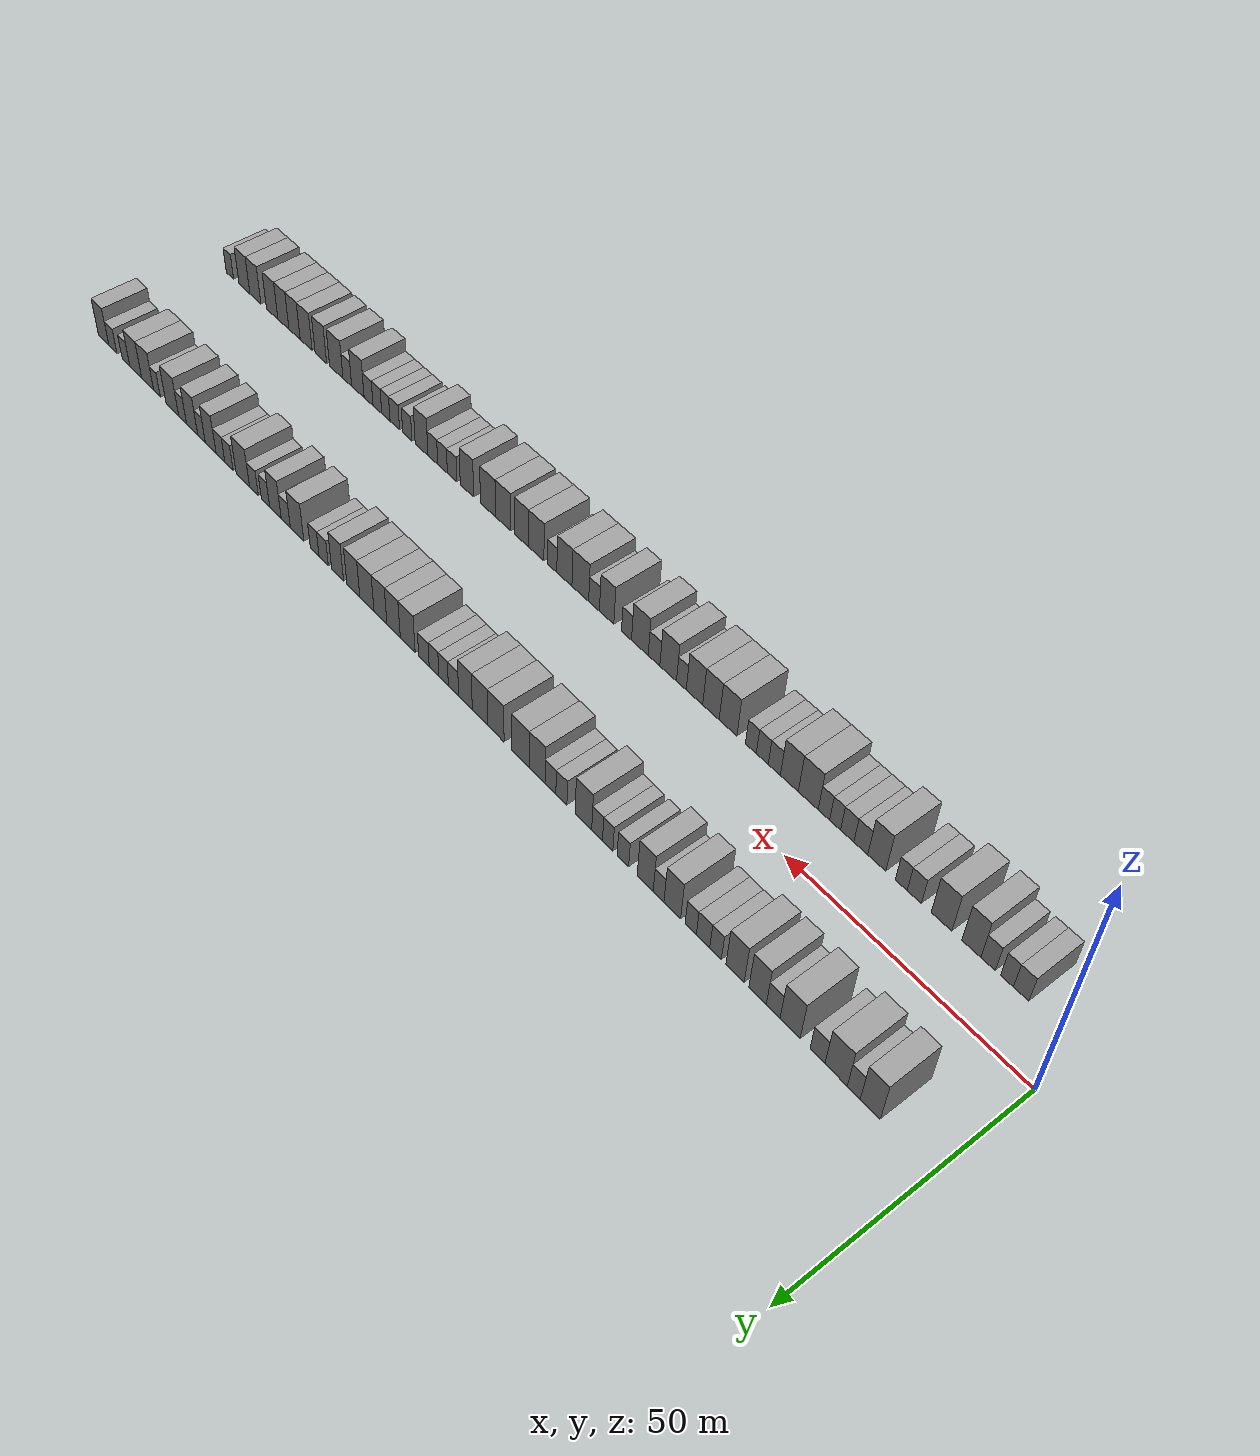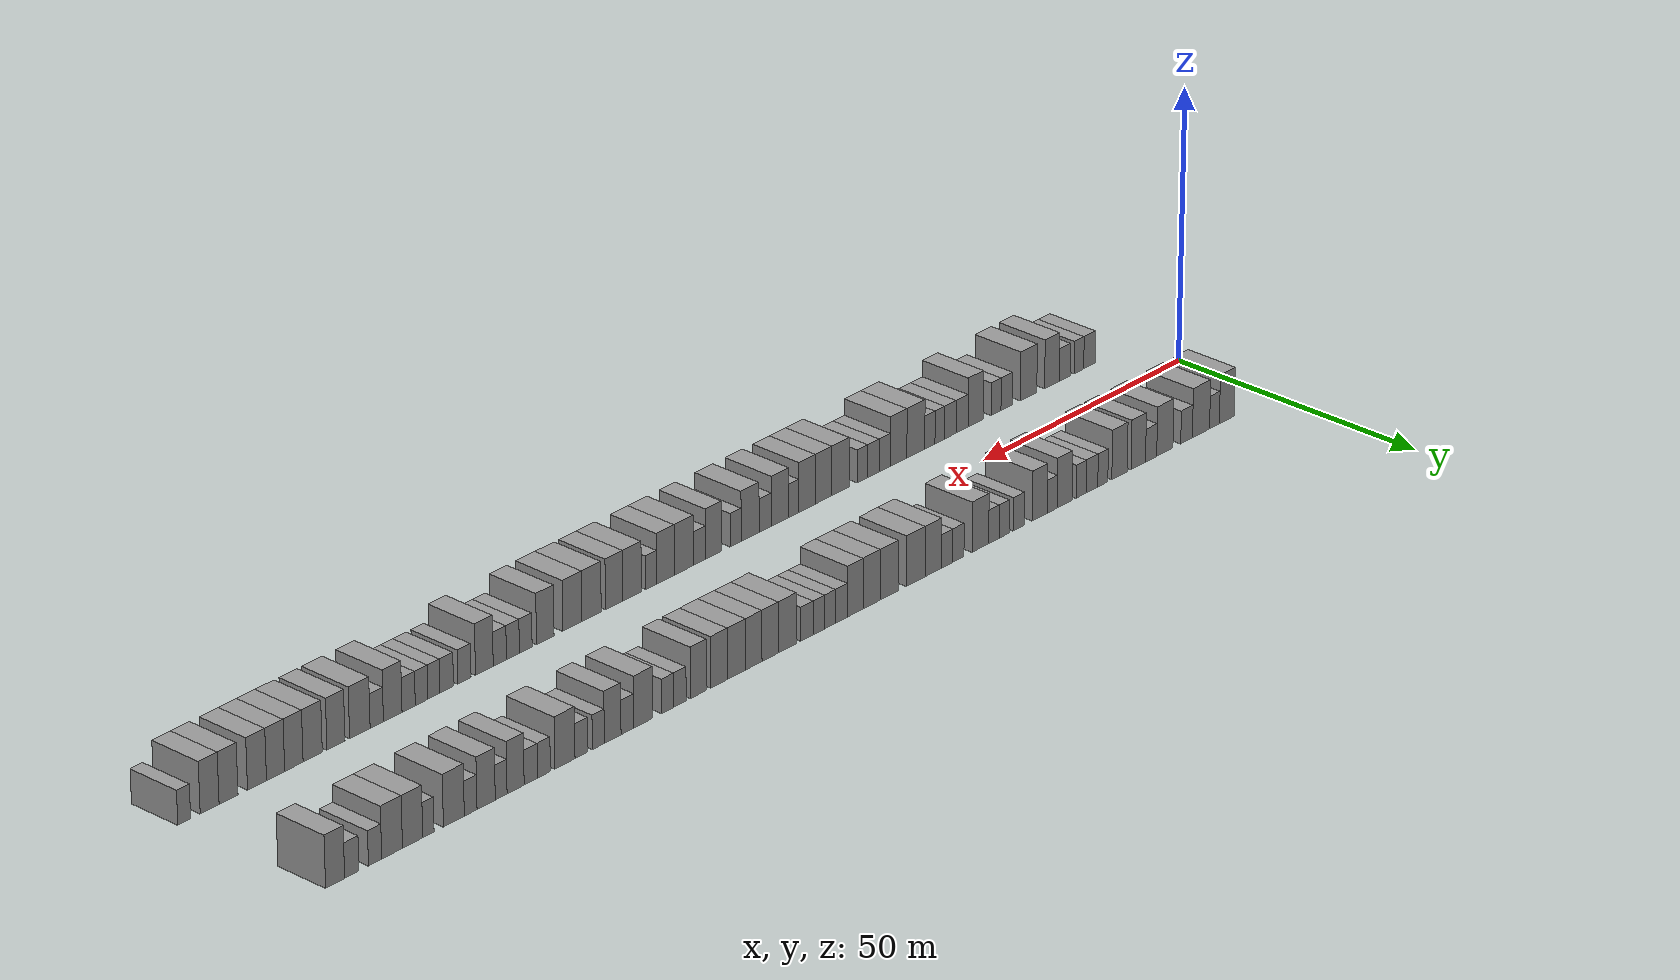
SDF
<sdf version="1.6">
 <world name="default">
  <scene>
   <sky><clouds><speed>12</speed></clouds></sky>
   <ambient>0.4 0.4 0.4 1</ambient>
   <background>0.7 0.7 0.7 1</background>
   <shadows>1</shadows>
  </scene>
  <gravity>0 0 -9.8066</gravity>
  <magnetic_field>6e-06 2.3e-05 -4.2e-05</magnetic_field>
  <physics default="0" name="default_physics" type="ode">
   <ode>
    <solver>
     <type>quick</type>
     <iters>10</iters>
     <sor>1.0</sor>
     <use_dynamic_moi_rescaling>0</use_dynamic_moi_rescaling>
    </solver>
    <constraints>
     <cfm>0</cfm>
     <erp>0.2</erp>
     <contact_max_correcting_vel>100</contact_max_correcting_vel>
     <contact_surface_layer>0.001</contact_surface_layer>
    </constraints>
   </ode>
   <max_step_size>0.004</max_step_size>
   <real_time_factor>1</real_time_factor>
   <real_time_update_rate>250</real_time_update_rate>
  </physics>
  <light name="sun" type="directional">
   <pose>0 0 10 0 0 0</pose>
   <diffuse>0.8 0.8 0.8 1</diffuse>
   <specular>0.2 0.2 0.2 1</specular>
   <attenuation>
    <range>1000</range>
    <constant>0.9</constant>
    <linear>0.01</linear>
    <quadratic>0.001</quadratic>
   </attenuation>
   <direction>-0.5 0.1 -0.9</direction>
  </light>
  <model name="building_1">
   <static>1</static>
   <pose>11.9355 15.0000 0 0.000000 0.000000 1.570796</pose>
   <link name="link">
    <pose>0 0 4.50 0 0 0</pose>
    <collision name="collision"><geometry><box><size>10.0000 3.8709 9.0000</size></box></geometry></collision>
    <visual name="visual">
     <cast_shadows>0</cast_shadows>
     <geometry><box><size>10.0000 3.8709 9.0000</size></box></geometry>
     <material>
      <script>
       <uri>model://grey_wall/materials/scripts</uri>
       <uri>model://grey_wall/materials/textures</uri>
       <name>vrc/grey_wall</name>
      </script>
     </material>
    </visual>
   </link>
  </model>
  <model name="building_2">
   <static>1</static>
   <pose>15.1357 15.0000 0 0.000000 0.000000 1.570796</pose>
   <link name="link">
    <pose>0 0 3.00 0 0 0</pose>
    <collision name="collision"><geometry><box><size>10.0000 2.5296 6.0000</size></box></geometry></collision>
    <visual name="visual">
     <cast_shadows>0</cast_shadows>
     <geometry><box><size>10.0000 2.5296 6.0000</size></box></geometry>
     <material>
      <script>
       <uri>model://grey_wall/materials/scripts</uri>
       <uri>model://grey_wall/materials/textures</uri>
       <name>vrc/grey_wall</name>
      </script>
     </material>
    </visual>
   </link>
  </model>
  <model name="building_3">
   <static>1</static>
   <pose>18.6159 15.0000 0 0.000000 0.000000 1.570796</pose>
   <link name="link">
    <pose>0 0 4.50 0 0 0</pose>
    <collision name="collision"><geometry><box><size>10.0000 4.4307 9.0000</size></box></geometry></collision>
    <visual name="visual">
     <cast_shadows>0</cast_shadows>
     <geometry><box><size>10.0000 4.4307 9.0000</size></box></geometry>
     <material>
      <script>
       <uri>model://grey_wall/materials/scripts</uri>
       <uri>model://grey_wall/materials/textures</uri>
       <name>vrc/grey_wall</name>
      </script>
     </material>
    </visual>
   </link>
  </model>
  <model name="building_4">
   <static>1</static>
   <pose>22.3298 15.0000 0 0.000000 0.000000 1.570796</pose>
   <link name="link">
    <pose>0 0 3.00 0 0 0</pose>
    <collision name="collision"><geometry><box><size>10.0000 2.9972 6.0000</size></box></geometry></collision>
    <visual name="visual">
     <cast_shadows>0</cast_shadows>
     <geometry><box><size>10.0000 2.9972 6.0000</size></box></geometry>
     <material>
      <script>
       <uri>model://grey_wall/materials/scripts</uri>
       <uri>model://grey_wall/materials/textures</uri>
       <name>vrc/grey_wall</name>
      </script>
     </material>
    </visual>
   </link>
  </model>
  <model name="building_5">
   <static>1</static>
   <pose>27.8996 15.0000 0 0.000000 0.000000 1.570796</pose>
   <link name="link">
    <pose>0 0 4.50 0 0 0</pose>
    <collision name="collision"><geometry><box><size>10.0000 4.1425 9.0000</size></box></geometry></collision>
    <visual name="visual">
     <cast_shadows>0</cast_shadows>
     <geometry><box><size>10.0000 4.1425 9.0000</size></box></geometry>
     <material>
      <script>
       <uri>model://grey_wall/materials/scripts</uri>
       <uri>model://grey_wall/materials/textures</uri>
       <name>vrc/grey_wall</name>
      </script>
     </material>
    </visual>
   </link>
  </model>
  <model name="building_6">
   <static>1</static>
   <pose>31.3976 15.0000 0 0.000000 0.000000 1.570796</pose>
   <link name="link">
    <pose>0 0 3.00 0 0 0</pose>
    <collision name="collision"><geometry><box><size>10.0000 2.8534 6.0000</size></box></geometry></collision>
    <visual name="visual">
     <cast_shadows>0</cast_shadows>
     <geometry><box><size>10.0000 2.8534 6.0000</size></box></geometry>
     <material>
      <script>
       <uri>model://grey_wall/materials/scripts</uri>
       <uri>model://grey_wall/materials/textures</uri>
       <name>vrc/grey_wall</name>
      </script>
     </material>
    </visual>
   </link>
  </model>
  <model name="building_7">
   <static>1</static>
   <pose>34.6530 15.0000 0 0.000000 0.000000 1.570796</pose>
   <link name="link">
    <pose>0 0 4.50 0 0 0</pose>
    <collision name="collision"><geometry><box><size>10.0000 3.6575 9.0000</size></box></geometry></collision>
    <visual name="visual">
     <cast_shadows>0</cast_shadows>
     <geometry><box><size>10.0000 3.6575 9.0000</size></box></geometry>
     <material>
      <script>
       <uri>model://grey_wall/materials/scripts</uri>
       <uri>model://grey_wall/materials/textures</uri>
       <name>vrc/grey_wall</name>
      </script>
     </material>
    </visual>
   </link>
  </model>
  <model name="building_8">
   <static>1</static>
   <pose>39.4240 15.0000 0 0.000000 0.000000 1.570796</pose>
   <link name="link">
    <pose>0 0 4.50 0 0 0</pose>
    <collision name="collision"><geometry><box><size>10.0000 3.8845 9.0000</size></box></geometry></collision>
    <visual name="visual">
     <cast_shadows>0</cast_shadows>
     <geometry><box><size>10.0000 3.8845 9.0000</size></box></geometry>
     <material>
      <script>
       <uri>model://grey_wall/materials/scripts</uri>
       <uri>model://grey_wall/materials/textures</uri>
       <name>vrc/grey_wall</name>
      </script>
     </material>
    </visual>
   </link>
  </model>
  <model name="building_9">
   <static>1</static>
   <pose>43.6304 15.0000 0 0.000000 0.000000 1.570796</pose>
   <link name="link">
    <pose>0 0 3.00 0 0 0</pose>
    <collision name="collision"><geometry><box><size>10.0000 2.5283 6.0000</size></box></geometry></collision>
    <visual name="visual">
     <cast_shadows>0</cast_shadows>
     <geometry><box><size>10.0000 2.5283 6.0000</size></box></geometry>
     <material>
      <script>
       <uri>model://grey_wall/materials/scripts</uri>
       <uri>model://grey_wall/materials/textures</uri>
       <name>vrc/grey_wall</name>
      </script>
     </material>
    </visual>
   </link>
  </model>
  <model name="building_10">
   <static>1</static>
   <pose>46.3620 15.0000 0 0.000000 0.000000 1.570796</pose>
   <link name="link">
    <pose>0 0 3.00 0 0 0</pose>
    <collision name="collision"><geometry><box><size>10.0000 2.9349 6.0000</size></box></geometry></collision>
    <visual name="visual">
     <cast_shadows>0</cast_shadows>
     <geometry><box><size>10.0000 2.9349 6.0000</size></box></geometry>
     <material>
      <script>
       <uri>model://grey_wall/materials/scripts</uri>
       <uri>model://grey_wall/materials/textures</uri>
       <name>vrc/grey_wall</name>
      </script>
     </material>
    </visual>
   </link>
  </model>
  <model name="building_11">
   <static>1</static>
   <pose>49.0717 15.0000 0 0.000000 0.000000 1.570796</pose>
   <link name="link">
    <pose>0 0 3.00 0 0 0</pose>
    <collision name="collision"><geometry><box><size>10.0000 2.4846 6.0000</size></box></geometry></collision>
    <visual name="visual">
     <cast_shadows>0</cast_shadows>
     <geometry><box><size>10.0000 2.4846 6.0000</size></box></geometry>
     <material>
      <script>
       <uri>model://grey_wall/materials/scripts</uri>
       <uri>model://grey_wall/materials/textures</uri>
       <name>vrc/grey_wall</name>
      </script>
     </material>
    </visual>
   </link>
  </model>
  <model name="building_12">
   <static>1</static>
   <pose>53.1930 15.0000 0 0.000000 0.000000 1.570796</pose>
   <link name="link">
    <pose>0 0 4.50 0 0 0</pose>
    <collision name="collision"><geometry><box><size>10.0000 3.7579 9.0000</size></box></geometry></collision>
    <visual name="visual">
     <cast_shadows>0</cast_shadows>
     <geometry><box><size>10.0000 3.7579 9.0000</size></box></geometry>
     <material>
      <script>
       <uri>model://grey_wall/materials/scripts</uri>
       <uri>model://grey_wall/materials/textures</uri>
       <name>vrc/grey_wall</name>
      </script>
     </material>
    </visual>
   </link>
  </model>
  <model name="building_13">
   <static>1</static>
   <pose>56.2924 15.0000 0 0.000000 0.000000 1.570796</pose>
   <link name="link">
    <pose>0 0 3.00 0 0 0</pose>
    <collision name="collision"><geometry><box><size>10.0000 2.4409 6.0000</size></box></geometry></collision>
    <visual name="visual">
     <cast_shadows>0</cast_shadows>
     <geometry><box><size>10.0000 2.4409 6.0000</size></box></geometry>
     <material>
      <script>
       <uri>model://grey_wall/materials/scripts</uri>
       <uri>model://grey_wall/materials/textures</uri>
       <name>vrc/grey_wall</name>
      </script>
     </material>
    </visual>
   </link>
  </model>
  <model name="building_14">
   <static>1</static>
   <pose>59.3512 15.0000 0 0.000000 0.000000 1.570796</pose>
   <link name="link">
    <pose>0 0 4.50 0 0 0</pose>
    <collision name="collision"><geometry><box><size>10.0000 3.6767 9.0000</size></box></geometry></collision>
    <visual name="visual">
     <cast_shadows>0</cast_shadows>
     <geometry><box><size>10.0000 3.6767 9.0000</size></box></geometry>
     <material>
      <script>
       <uri>model://grey_wall/materials/scripts</uri>
       <uri>model://grey_wall/materials/textures</uri>
       <name>vrc/grey_wall</name>
      </script>
     </material>
    </visual>
   </link>
  </model>
  <model name="building_15">
   <static>1</static>
   <pose>64.5397 15.0000 0 0.000000 0.000000 1.570796</pose>
   <link name="link">
    <pose>0 0 3.00 0 0 0</pose>
    <collision name="collision"><geometry><box><size>10.0000 2.7004 6.0000</size></box></geometry></collision>
    <visual name="visual">
     <cast_shadows>0</cast_shadows>
     <geometry><box><size>10.0000 2.7004 6.0000</size></box></geometry>
     <material>
      <script>
       <uri>model://grey_wall/materials/scripts</uri>
       <uri>model://grey_wall/materials/textures</uri>
       <name>vrc/grey_wall</name>
      </script>
     </material>
    </visual>
   </link>
  </model>
  <model name="building_16">
   <static>1</static>
   <pose>68.1228 15.0000 0 0.000000 0.000000 1.570796</pose>
   <link name="link">
    <pose>0 0 3.00 0 0 0</pose>
    <collision name="collision"><geometry><box><size>10.0000 2.4657 6.0000</size></box></geometry></collision>
    <visual name="visual">
     <cast_shadows>0</cast_shadows>
     <geometry><box><size>10.0000 2.4657 6.0000</size></box></geometry>
     <material>
      <script>
       <uri>model://grey_wall/materials/scripts</uri>
       <uri>model://grey_wall/materials/textures</uri>
       <name>vrc/grey_wall</name>
      </script>
     </material>
    </visual>
   </link>
  </model>
  <model name="building_17">
   <static>1</static>
   <pose>70.6452 15.0000 0 0.000000 0.000000 1.570796</pose>
   <link name="link">
    <pose>0 0 3.00 0 0 0</pose>
    <collision name="collision"><geometry><box><size>10.0000 2.5791 6.0000</size></box></geometry></collision>
    <visual name="visual">
     <cast_shadows>0</cast_shadows>
     <geometry><box><size>10.0000 2.5791 6.0000</size></box></geometry>
     <material>
      <script>
       <uri>model://grey_wall/materials/scripts</uri>
       <uri>model://grey_wall/materials/textures</uri>
       <name>vrc/grey_wall</name>
      </script>
     </material>
    </visual>
   </link>
  </model>
  <model name="building_18">
   <static>1</static>
   <pose>73.9491 15.0000 0 0.000000 0.000000 1.570796</pose>
   <link name="link">
    <pose>0 0 4.50 0 0 0</pose>
    <collision name="collision"><geometry><box><size>10.0000 4.0286 9.0000</size></box></geometry></collision>
    <visual name="visual">
     <cast_shadows>0</cast_shadows>
     <geometry><box><size>10.0000 4.0286 9.0000</size></box></geometry>
     <material>
      <script>
       <uri>model://grey_wall/materials/scripts</uri>
       <uri>model://grey_wall/materials/textures</uri>
       <name>vrc/grey_wall</name>
      </script>
     </material>
    </visual>
   </link>
  </model>
  <model name="building_19">
   <static>1</static>
   <pose>79.3284 15.0000 0 0.000000 0.000000 1.570796</pose>
   <link name="link">
    <pose>0 0 3.00 0 0 0</pose>
    <collision name="collision"><geometry><box><size>10.0000 2.7300 6.0000</size></box></geometry></collision>
    <visual name="visual">
     <cast_shadows>0</cast_shadows>
     <geometry><box><size>10.0000 2.7300 6.0000</size></box></geometry>
     <material>
      <script>
       <uri>model://grey_wall/materials/scripts</uri>
       <uri>model://grey_wall/materials/textures</uri>
       <name>vrc/grey_wall</name>
      </script>
     </material>
    </visual>
   </link>
  </model>
  <model name="building_20">
   <static>1</static>
   <pose>82.0445 15.0000 0 0.000000 0.000000 1.570796</pose>
   <link name="link">
    <pose>0 0 3.00 0 0 0</pose>
    <collision name="collision"><geometry><box><size>10.0000 2.7021 6.0000</size></box></geometry></collision>
    <visual name="visual">
     <cast_shadows>0</cast_shadows>
     <geometry><box><size>10.0000 2.7021 6.0000</size></box></geometry>
     <material>
      <script>
       <uri>model://grey_wall/materials/scripts</uri>
       <uri>model://grey_wall/materials/textures</uri>
       <name>vrc/grey_wall</name>
      </script>
     </material>
    </visual>
   </link>
  </model>
  <model name="building_21">
   <static>1</static>
   <pose>85.3691 15.0000 0 0.000000 0.000000 1.570796</pose>
   <link name="link">
    <pose>0 0 4.50 0 0 0</pose>
    <collision name="collision"><geometry><box><size>10.0000 3.9471 9.0000</size></box></geometry></collision>
    <visual name="visual">
     <cast_shadows>0</cast_shadows>
     <geometry><box><size>10.0000 3.9471 9.0000</size></box></geometry>
     <material>
      <script>
       <uri>model://grey_wall/materials/scripts</uri>
       <uri>model://grey_wall/materials/textures</uri>
       <name>vrc/grey_wall</name>
      </script>
     </material>
    </visual>
   </link>
  </model>
  <model name="building_22">
   <static>1</static>
   <pose>89.5817 15.0000 0 0.000000 0.000000 1.570796</pose>
   <link name="link">
    <pose>0 0 4.50 0 0 0</pose>
    <collision name="collision"><geometry><box><size>10.0000 4.4781 9.0000</size></box></geometry></collision>
    <visual name="visual">
     <cast_shadows>0</cast_shadows>
     <geometry><box><size>10.0000 4.4781 9.0000</size></box></geometry>
     <material>
      <script>
       <uri>model://grey_wall/materials/scripts</uri>
       <uri>model://grey_wall/materials/textures</uri>
       <name>vrc/grey_wall</name>
      </script>
     </material>
    </visual>
   </link>
  </model>
  <model name="building_23">
   <static>1</static>
   <pose>95.9513 15.0000 0 0.000000 0.000000 1.570796</pose>
   <link name="link">
    <pose>0 0 4.50 0 0 0</pose>
    <collision name="collision"><geometry><box><size>10.0000 4.2611 9.0000</size></box></geometry></collision>
    <visual name="visual">
     <cast_shadows>0</cast_shadows>
     <geometry><box><size>10.0000 4.2611 9.0000</size></box></geometry>
     <material>
      <script>
       <uri>model://grey_wall/materials/scripts</uri>
       <uri>model://grey_wall/materials/textures</uri>
       <name>vrc/grey_wall</name>
      </script>
     </material>
    </visual>
   </link>
  </model>
  <model name="building_24">
   <static>1</static>
   <pose>100.1310 15.0000 0 0.000000 0.000000 1.570796</pose>
   <link name="link">
    <pose>0 0 4.50 0 0 0</pose>
    <collision name="collision"><geometry><box><size>10.0000 4.0983 9.0000</size></box></geometry></collision>
    <visual name="visual">
     <cast_shadows>0</cast_shadows>
     <geometry><box><size>10.0000 4.0983 9.0000</size></box></geometry>
     <material>
      <script>
       <uri>model://grey_wall/materials/scripts</uri>
       <uri>model://grey_wall/materials/textures</uri>
       <name>vrc/grey_wall</name>
      </script>
     </material>
    </visual>
   </link>
  </model>
  <model name="building_25">
   <static>1</static>
   <pose>104.0064 15.0000 0 0.000000 0.000000 1.570796</pose>
   <link name="link">
    <pose>0 0 4.50 0 0 0</pose>
    <collision name="collision"><geometry><box><size>10.0000 3.6526 9.0000</size></box></geometry></collision>
    <visual name="visual">
     <cast_shadows>0</cast_shadows>
     <geometry><box><size>10.0000 3.6526 9.0000</size></box></geometry>
     <material>
      <script>
       <uri>model://grey_wall/materials/scripts</uri>
       <uri>model://grey_wall/materials/textures</uri>
       <name>vrc/grey_wall</name>
      </script>
     </material>
    </visual>
   </link>
  </model>
  <model name="building_26">
   <static>1</static>
   <pose>107.2340 15.0000 0 0.000000 0.000000 1.570796</pose>
   <link name="link">
    <pose>0 0 3.00 0 0 0</pose>
    <collision name="collision"><geometry><box><size>10.0000 2.8026 6.0000</size></box></geometry></collision>
    <visual name="visual">
     <cast_shadows>0</cast_shadows>
     <geometry><box><size>10.0000 2.8026 6.0000</size></box></geometry>
     <material>
      <script>
       <uri>model://grey_wall/materials/scripts</uri>
       <uri>model://grey_wall/materials/textures</uri>
       <name>vrc/grey_wall</name>
      </script>
     </material>
    </visual>
   </link>
  </model>
  <model name="building_27">
   <static>1</static>
   <pose>109.9182 15.0000 0 0.000000 0.000000 1.570796</pose>
   <link name="link">
    <pose>0 0 3.00 0 0 0</pose>
    <collision name="collision"><geometry><box><size>10.0000 2.5657 6.0000</size></box></geometry></collision>
    <visual name="visual">
     <cast_shadows>0</cast_shadows>
     <geometry><box><size>10.0000 2.5657 6.0000</size></box></geometry>
     <material>
      <script>
       <uri>model://grey_wall/materials/scripts</uri>
       <uri>model://grey_wall/materials/textures</uri>
       <name>vrc/grey_wall</name>
      </script>
     </material>
    </visual>
   </link>
  </model>
  <model name="building_28">
   <static>1</static>
   <pose>112.5462 15.0000 0 0.000000 0.000000 1.570796</pose>
   <link name="link">
    <pose>0 0 3.00 0 0 0</pose>
    <collision name="collision"><geometry><box><size>10.0000 2.6904 6.0000</size></box></geometry></collision>
    <visual name="visual">
     <cast_shadows>0</cast_shadows>
     <geometry><box><size>10.0000 2.6904 6.0000</size></box></geometry>
     <material>
      <script>
       <uri>model://grey_wall/materials/scripts</uri>
       <uri>model://grey_wall/materials/textures</uri>
       <name>vrc/grey_wall</name>
      </script>
     </material>
    </visual>
   </link>
  </model>
  <model name="building_29">
   <static>1</static>
   <pose>115.3470 15.0000 0 0.000000 0.000000 1.570796</pose>
   <link name="link">
    <pose>0 0 3.00 0 0 0</pose>
    <collision name="collision"><geometry><box><size>10.0000 2.9112 6.0000</size></box></geometry></collision>
    <visual name="visual">
     <cast_shadows>0</cast_shadows>
     <geometry><box><size>10.0000 2.9112 6.0000</size></box></geometry>
     <material>
      <script>
       <uri>model://grey_wall/materials/scripts</uri>
       <uri>model://grey_wall/materials/textures</uri>
       <name>vrc/grey_wall</name>
      </script>
     </material>
    </visual>
   </link>
  </model>
  <model name="building_30">
   <static>1</static>
   <pose>119.9015 15.0000 0 0.000000 0.000000 1.570796</pose>
   <link name="link">
    <pose>0 0 4.50 0 0 0</pose>
    <collision name="collision"><geometry><box><size>10.0000 4.1978 9.0000</size></box></geometry></collision>
    <visual name="visual">
     <cast_shadows>0</cast_shadows>
     <geometry><box><size>10.0000 4.1978 9.0000</size></box></geometry>
     <material>
      <script>
       <uri>model://grey_wall/materials/scripts</uri>
       <uri>model://grey_wall/materials/textures</uri>
       <name>vrc/grey_wall</name>
      </script>
     </material>
    </visual>
   </link>
  </model>
  <model name="building_31">
   <static>1</static>
   <pose>123.9093 15.0000 0 0.000000 0.000000 1.570796</pose>
   <link name="link">
    <pose>0 0 4.50 0 0 0</pose>
    <collision name="collision"><geometry><box><size>10.0000 3.8177 9.0000</size></box></geometry></collision>
    <visual name="visual">
     <cast_shadows>0</cast_shadows>
     <geometry><box><size>10.0000 3.8177 9.0000</size></box></geometry>
     <material>
      <script>
       <uri>model://grey_wall/materials/scripts</uri>
       <uri>model://grey_wall/materials/textures</uri>
       <name>vrc/grey_wall</name>
      </script>
     </material>
    </visual>
   </link>
  </model>
  <model name="building_32">
   <static>1</static>
   <pose>127.6894 15.0000 0 0.000000 0.000000 1.570796</pose>
   <link name="link">
    <pose>0 0 4.50 0 0 0</pose>
    <collision name="collision"><geometry><box><size>10.0000 3.7425 9.0000</size></box></geometry></collision>
    <visual name="visual">
     <cast_shadows>0</cast_shadows>
     <geometry><box><size>10.0000 3.7425 9.0000</size></box></geometry>
     <material>
      <script>
       <uri>model://grey_wall/materials/scripts</uri>
       <uri>model://grey_wall/materials/textures</uri>
       <name>vrc/grey_wall</name>
      </script>
     </material>
    </visual>
   </link>
  </model>
  <model name="building_33">
   <static>1</static>
   <pose>131.6490 15.0000 0 0.000000 0.000000 1.570796</pose>
   <link name="link">
    <pose>0 0 4.50 0 0 0</pose>
    <collision name="collision"><geometry><box><size>10.0000 4.1766 9.0000</size></box></geometry></collision>
    <visual name="visual">
     <cast_shadows>0</cast_shadows>
     <geometry><box><size>10.0000 4.1766 9.0000</size></box></geometry>
     <material>
      <script>
       <uri>model://grey_wall/materials/scripts</uri>
       <uri>model://grey_wall/materials/textures</uri>
       <name>vrc/grey_wall</name>
      </script>
     </material>
    </visual>
   </link>
  </model>
  <model name="building_34">
   <static>1</static>
   <pose>135.6532 15.0000 0 0.000000 0.000000 1.570796</pose>
   <link name="link">
    <pose>0 0 4.50 0 0 0</pose>
    <collision name="collision"><geometry><box><size>10.0000 3.8319 9.0000</size></box></geometry></collision>
    <visual name="visual">
     <cast_shadows>0</cast_shadows>
     <geometry><box><size>10.0000 3.8319 9.0000</size></box></geometry>
     <material>
      <script>
       <uri>model://grey_wall/materials/scripts</uri>
       <uri>model://grey_wall/materials/textures</uri>
       <name>vrc/grey_wall</name>
      </script>
     </material>
    </visual>
   </link>
  </model>
  <model name="building_35">
   <static>1</static>
   <pose>140.3760 15.0000 0 0.000000 0.000000 1.570796</pose>
   <link name="link">
    <pose>0 0 4.50 0 0 0</pose>
    <collision name="collision"><geometry><box><size>10.0000 3.6137 9.0000</size></box></geometry></collision>
    <visual name="visual">
     <cast_shadows>0</cast_shadows>
     <geometry><box><size>10.0000 3.6137 9.0000</size></box></geometry>
     <material>
      <script>
       <uri>model://grey_wall/materials/scripts</uri>
       <uri>model://grey_wall/materials/textures</uri>
       <name>vrc/grey_wall</name>
      </script>
     </material>
    </visual>
   </link>
  </model>
  <model name="building_36">
   <static>1</static>
   <pose>144.5920 15.0000 0 0.000000 0.000000 1.570796</pose>
   <link name="link">
    <pose>0 0 3.00 0 0 0</pose>
    <collision name="collision"><geometry><box><size>10.0000 2.8183 6.0000</size></box></geometry></collision>
    <visual name="visual">
     <cast_shadows>0</cast_shadows>
     <geometry><box><size>10.0000 2.8183 6.0000</size></box></geometry>
     <material>
      <script>
       <uri>model://grey_wall/materials/scripts</uri>
       <uri>model://grey_wall/materials/textures</uri>
       <name>vrc/grey_wall</name>
      </script>
     </material>
    </visual>
   </link>
  </model>
  <model name="building_37">
   <static>1</static>
   <pose>147.3561 15.0000 0 0.000000 0.000000 1.570796</pose>
   <link name="link">
    <pose>0 0 3.00 0 0 0</pose>
    <collision name="collision"><geometry><box><size>10.0000 2.7098 6.0000</size></box></geometry></collision>
    <visual name="visual">
     <cast_shadows>0</cast_shadows>
     <geometry><box><size>10.0000 2.7098 6.0000</size></box></geometry>
     <material>
      <script>
       <uri>model://grey_wall/materials/scripts</uri>
       <uri>model://grey_wall/materials/textures</uri>
       <name>vrc/grey_wall</name>
      </script>
     </material>
    </visual>
   </link>
  </model>
  <model name="building_38">
   <static>1</static>
   <pose>152.8337 15.0000 0 0.000000 0.000000 1.570796</pose>
   <link name="link">
    <pose>0 0 4.50 0 0 0</pose>
    <collision name="collision"><geometry><box><size>10.0000 4.2455 9.0000</size></box></geometry></collision>
    <visual name="visual">
     <cast_shadows>0</cast_shadows>
     <geometry><box><size>10.0000 4.2455 9.0000</size></box></geometry>
     <material>
      <script>
       <uri>model://grey_wall/materials/scripts</uri>
       <uri>model://grey_wall/materials/textures</uri>
       <name>vrc/grey_wall</name>
      </script>
     </material>
    </visual>
   </link>
  </model>
  <model name="building_39">
   <static>1</static>
   <pose>156.4042 15.0000 0 0.000000 0.000000 1.570796</pose>
   <link name="link">
    <pose>0 0 3.00 0 0 0</pose>
    <collision name="collision"><geometry><box><size>10.0000 2.8953 6.0000</size></box></geometry></collision>
    <visual name="visual">
     <cast_shadows>0</cast_shadows>
     <geometry><box><size>10.0000 2.8953 6.0000</size></box></geometry>
     <material>
      <script>
       <uri>model://grey_wall/materials/scripts</uri>
       <uri>model://grey_wall/materials/textures</uri>
       <name>vrc/grey_wall</name>
      </script>
     </material>
    </visual>
   </link>
  </model>
  <model name="building_40">
   <static>1</static>
   <pose>159.7042 15.0000 0 0.000000 0.000000 1.570796</pose>
   <link name="link">
    <pose>0 0 4.50 0 0 0</pose>
    <collision name="collision"><geometry><box><size>10.0000 3.7048 9.0000</size></box></geometry></collision>
    <visual name="visual">
     <cast_shadows>0</cast_shadows>
     <geometry><box><size>10.0000 3.7048 9.0000</size></box></geometry>
     <material>
      <script>
       <uri>model://grey_wall/materials/scripts</uri>
       <uri>model://grey_wall/materials/textures</uri>
       <name>vrc/grey_wall</name>
      </script>
     </material>
    </visual>
   </link>
  </model>
  <model name="building_41">
   <static>1</static>
   <pose>162.8913 15.0000 0 0.000000 0.000000 1.570796</pose>
   <link name="link">
    <pose>0 0 3.00 0 0 0</pose>
    <collision name="collision"><geometry><box><size>10.0000 2.6694 6.0000</size></box></geometry></collision>
    <visual name="visual">
     <cast_shadows>0</cast_shadows>
     <geometry><box><size>10.0000 2.6694 6.0000</size></box></geometry>
     <material>
      <script>
       <uri>model://grey_wall/materials/scripts</uri>
       <uri>model://grey_wall/materials/textures</uri>
       <name>vrc/grey_wall</name>
      </script>
     </material>
    </visual>
   </link>
  </model>
  <model name="building_42">
   <static>1</static>
   <pose>166.6520 15.0000 0 0.000000 0.000000 1.570796</pose>
   <link name="link">
    <pose>0 0 3.00 0 0 0</pose>
    <collision name="collision"><geometry><box><size>10.0000 2.8520 6.0000</size></box></geometry></collision>
    <visual name="visual">
     <cast_shadows>0</cast_shadows>
     <geometry><box><size>10.0000 2.8520 6.0000</size></box></geometry>
     <material>
      <script>
       <uri>model://grey_wall/materials/scripts</uri>
       <uri>model://grey_wall/materials/textures</uri>
       <name>vrc/grey_wall</name>
      </script>
     </material>
    </visual>
   </link>
  </model>
  <model name="building_43">
   <static>1</static>
   <pose>170.2901 15.0000 0 0.000000 0.000000 1.570796</pose>
   <link name="link">
    <pose>0 0 4.50 0 0 0</pose>
    <collision name="collision"><geometry><box><size>10.0000 4.4242 9.0000</size></box></geometry></collision>
    <visual name="visual">
     <cast_shadows>0</cast_shadows>
     <geometry><box><size>10.0000 4.4242 9.0000</size></box></geometry>
     <material>
      <script>
       <uri>model://grey_wall/materials/scripts</uri>
       <uri>model://grey_wall/materials/textures</uri>
       <name>vrc/grey_wall</name>
      </script>
     </material>
    </visual>
   </link>
  </model>
  <model name="building_44">
   <static>1</static>
   <pose>174.8964 15.0000 0 0.000000 0.000000 1.570796</pose>
   <link name="link">
    <pose>0 0 3.00 0 0 0</pose>
    <collision name="collision"><geometry><box><size>10.0000 2.7885 6.0000</size></box></geometry></collision>
    <visual name="visual">
     <cast_shadows>0</cast_shadows>
     <geometry><box><size>10.0000 2.7885 6.0000</size></box></geometry>
     <material>
      <script>
       <uri>model://grey_wall/materials/scripts</uri>
       <uri>model://grey_wall/materials/textures</uri>
       <name>vrc/grey_wall</name>
      </script>
     </material>
    </visual>
   </link>
  </model>
  <model name="building_45">
   <static>1</static>
   <pose>177.7703 15.0000 0 0.000000 0.000000 1.570796</pose>
   <link name="link">
    <pose>0 0 3.00 0 0 0</pose>
    <collision name="collision"><geometry><box><size>10.0000 2.9592 6.0000</size></box></geometry></collision>
    <visual name="visual">
     <cast_shadows>0</cast_shadows>
     <geometry><box><size>10.0000 2.9592 6.0000</size></box></geometry>
     <material>
      <script>
       <uri>model://grey_wall/materials/scripts</uri>
       <uri>model://grey_wall/materials/textures</uri>
       <name>vrc/grey_wall</name>
      </script>
     </material>
    </visual>
   </link>
  </model>
  <model name="building_46">
   <static>1</static>
   <pose>181.1116 15.0000 0 0.000000 0.000000 1.570796</pose>
   <link name="link">
    <pose>0 0 4.50 0 0 0</pose>
    <collision name="collision"><geometry><box><size>10.0000 3.7234 9.0000</size></box></geometry></collision>
    <visual name="visual">
     <cast_shadows>0</cast_shadows>
     <geometry><box><size>10.0000 3.7234 9.0000</size></box></geometry>
     <material>
      <script>
       <uri>model://grey_wall/materials/scripts</uri>
       <uri>model://grey_wall/materials/textures</uri>
       <name>vrc/grey_wall</name>
      </script>
     </material>
    </visual>
   </link>
  </model>
  <model name="building_47">
   <static>1</static>
   <pose>184.2537 15.0000 0 0.000000 0.000000 1.570796</pose>
   <link name="link">
    <pose>0 0 3.00 0 0 0</pose>
    <collision name="collision"><geometry><box><size>10.0000 2.5609 6.0000</size></box></geometry></collision>
    <visual name="visual">
     <cast_shadows>0</cast_shadows>
     <geometry><box><size>10.0000 2.5609 6.0000</size></box></geometry>
     <material>
      <script>
       <uri>model://grey_wall/materials/scripts</uri>
       <uri>model://grey_wall/materials/textures</uri>
       <name>vrc/grey_wall</name>
      </script>
     </material>
    </visual>
   </link>
  </model>
  <model name="building_48">
   <static>1</static>
   <pose>187.5087 15.0000 0 0.000000 0.000000 1.570796</pose>
   <link name="link">
    <pose>0 0 4.50 0 0 0</pose>
    <collision name="collision"><geometry><box><size>10.0000 3.9491 9.0000</size></box></geometry></collision>
    <visual name="visual">
     <cast_shadows>0</cast_shadows>
     <geometry><box><size>10.0000 3.9491 9.0000</size></box></geometry>
     <material>
      <script>
       <uri>model://grey_wall/materials/scripts</uri>
       <uri>model://grey_wall/materials/textures</uri>
       <name>vrc/grey_wall</name>
      </script>
     </material>
    </visual>
   </link>
  </model>
  <model name="building_49">
   <static>1</static>
   <pose>190.8543 15.0000 0 0.000000 0.000000 1.570796</pose>
   <link name="link">
    <pose>0 0 3.00 0 0 0</pose>
    <collision name="collision"><geometry><box><size>10.0000 2.7420 6.0000</size></box></geometry></collision>
    <visual name="visual">
     <cast_shadows>0</cast_shadows>
     <geometry><box><size>10.0000 2.7420 6.0000</size></box></geometry>
     <material>
      <script>
       <uri>model://grey_wall/materials/scripts</uri>
       <uri>model://grey_wall/materials/textures</uri>
       <name>vrc/grey_wall</name>
      </script>
     </material>
    </visual>
   </link>
  </model>
  <model name="building_50">
   <static>1</static>
   <pose>194.4691 15.0000 0 0.000000 0.000000 1.570796</pose>
   <link name="link">
    <pose>0 0 4.50 0 0 0</pose>
    <collision name="collision"><geometry><box><size>10.0000 4.4876 9.0000</size></box></geometry></collision>
    <visual name="visual">
     <cast_shadows>0</cast_shadows>
     <geometry><box><size>10.0000 4.4876 9.0000</size></box></geometry>
     <material>
      <script>
       <uri>model://grey_wall/materials/scripts</uri>
       <uri>model://grey_wall/materials/textures</uri>
       <name>vrc/grey_wall</name>
      </script>
     </material>
    </visual>
   </link>
  </model>
  <model name="building_51">
   <static>1</static>
   <pose>199.9189 15.0000 0 0.000000 0.000000 1.570796</pose>
   <link name="link">
    <pose>0 0 3.00 0 0 0</pose>
    <collision name="collision"><geometry><box><size>10.0000 2.4120 6.0000</size></box></geometry></collision>
    <visual name="visual">
     <cast_shadows>0</cast_shadows>
     <geometry><box><size>10.0000 2.4120 6.0000</size></box></geometry>
     <material>
      <script>
       <uri>model://grey_wall/materials/scripts</uri>
       <uri>model://grey_wall/materials/textures</uri>
       <name>vrc/grey_wall</name>
      </script>
     </material>
    </visual>
   </link>
  </model>
  <model name="building_52">
   <static>1</static>
   <pose>203.2819 15.0000 0 0.000000 0.000000 1.570796</pose>
   <link name="link">
    <pose>0 0 4.50 0 0 0</pose>
    <collision name="collision"><geometry><box><size>10.0000 4.3141 9.0000</size></box></geometry></collision>
    <visual name="visual">
     <cast_shadows>0</cast_shadows>
     <geometry><box><size>10.0000 4.3141 9.0000</size></box></geometry>
     <material>
      <script>
       <uri>model://grey_wall/materials/scripts</uri>
       <uri>model://grey_wall/materials/textures</uri>
       <name>vrc/grey_wall</name>
      </script>
     </material>
    </visual>
   </link>
  </model>
  <model name="building_53">
   <static>1</static>
   <pose>207.6376 15.0000 0 0.000000 0.000000 1.570796</pose>
   <link name="link">
    <pose>0 0 4.50 0 0 0</pose>
    <collision name="collision"><geometry><box><size>10.0000 4.3973 9.0000</size></box></geometry></collision>
    <visual name="visual">
     <cast_shadows>0</cast_shadows>
     <geometry><box><size>10.0000 4.3973 9.0000</size></box></geometry>
     <material>
      <script>
       <uri>model://grey_wall/materials/scripts</uri>
       <uri>model://grey_wall/materials/textures</uri>
       <name>vrc/grey_wall</name>
      </script>
     </material>
    </visual>
   </link>
  </model>
  <model name="building_54">
   <static>1</static>
   <pose>211.2331 15.0000 0 0.000000 0.000000 1.570796</pose>
   <link name="link">
    <pose>0 0 3.00 0 0 0</pose>
    <collision name="collision"><geometry><box><size>10.0000 2.7936 6.0000</size></box></geometry></collision>
    <visual name="visual">
     <cast_shadows>0</cast_shadows>
     <geometry><box><size>10.0000 2.7936 6.0000</size></box></geometry>
     <material>
      <script>
       <uri>model://grey_wall/materials/scripts</uri>
       <uri>model://grey_wall/materials/textures</uri>
       <name>vrc/grey_wall</name>
      </script>
     </material>
    </visual>
   </link>
  </model>
  <model name="building_55">
   <static>1</static>
   <pose>216.1294 15.0000 0 0.000000 0.000000 1.570796</pose>
   <link name="link">
    <pose>0 0 3.00 0 0 0</pose>
    <collision name="collision"><geometry><box><size>10.0000 2.9991 6.0000</size></box></geometry></collision>
    <visual name="visual">
     <cast_shadows>0</cast_shadows>
     <geometry><box><size>10.0000 2.9991 6.0000</size></box></geometry>
     <material>
      <script>
       <uri>model://grey_wall/materials/scripts</uri>
       <uri>model://grey_wall/materials/textures</uri>
       <name>vrc/grey_wall</name>
      </script>
     </material>
    </visual>
   </link>
  </model>
  <model name="building_56">
   <static>1</static>
   <pose>219.6202 15.0000 0 0.000000 0.000000 1.570796</pose>
   <link name="link">
    <pose>0 0 4.50 0 0 0</pose>
    <collision name="collision"><geometry><box><size>10.0000 3.9824 9.0000</size></box></geometry></collision>
    <visual name="visual">
     <cast_shadows>0</cast_shadows>
     <geometry><box><size>10.0000 3.9824 9.0000</size></box></geometry>
     <material>
      <script>
       <uri>model://grey_wall/materials/scripts</uri>
       <uri>model://grey_wall/materials/textures</uri>
       <name>vrc/grey_wall</name>
      </script>
     </material>
    </visual>
   </link>
  </model>
  <model name="building_57">
   <static>1</static>
   <pose>11.4850 -15.0000 0 0.000000 0.000000 1.570796</pose>
   <link name="link">
    <pose>0 0 3.00 0 0 0</pose>
    <collision name="collision"><geometry><box><size>10.0000 2.9699 6.0000</size></box></geometry></collision>
    <visual name="visual">
     <cast_shadows>0</cast_shadows>
     <geometry><box><size>10.0000 2.9699 6.0000</size></box></geometry>
     <material>
      <script>
       <uri>model://grey_wall/materials/scripts</uri>
       <uri>model://grey_wall/materials/textures</uri>
       <name>vrc/grey_wall</name>
      </script>
     </material>
    </visual>
   </link>
  </model>
  <model name="building_58">
   <static>1</static>
   <pose>14.2070 -15.0000 0 0.000000 0.000000 1.570796</pose>
   <link name="link">
    <pose>0 0 3.00 0 0 0</pose>
    <collision name="collision"><geometry><box><size>10.0000 2.4742 6.0000</size></box></geometry></collision>
    <visual name="visual">
     <cast_shadows>0</cast_shadows>
     <geometry><box><size>10.0000 2.4742 6.0000</size></box></geometry>
     <material>
      <script>
       <uri>model://grey_wall/materials/scripts</uri>
       <uri>model://grey_wall/materials/textures</uri>
       <name>vrc/grey_wall</name>
      </script>
     </material>
    </visual>
   </link>
  </model>
  <model name="building_59">
   <static>1</static>
   <pose>17.8604 -15.0000 0 0.000000 0.000000 1.570796</pose>
   <link name="link">
    <pose>0 0 3.00 0 0 0</pose>
    <collision name="collision"><geometry><box><size>10.0000 2.8324 6.0000</size></box></geometry></collision>
    <visual name="visual">
     <cast_shadows>0</cast_shadows>
     <geometry><box><size>10.0000 2.8324 6.0000</size></box></geometry>
     <material>
      <script>
       <uri>model://grey_wall/materials/scripts</uri>
       <uri>model://grey_wall/materials/textures</uri>
       <name>vrc/grey_wall</name>
      </script>
     </material>
    </visual>
   </link>
  </model>
  <model name="building_60">
   <static>1</static>
   <pose>21.1529 -15.0000 0 0.000000 0.000000 1.570796</pose>
   <link name="link">
    <pose>0 0 4.50 0 0 0</pose>
    <collision name="collision"><geometry><box><size>10.0000 3.7526 9.0000</size></box></geometry></collision>
    <visual name="visual">
     <cast_shadows>0</cast_shadows>
     <geometry><box><size>10.0000 3.7526 9.0000</size></box></geometry>
     <material>
      <script>
       <uri>model://grey_wall/materials/scripts</uri>
       <uri>model://grey_wall/materials/textures</uri>
       <name>vrc/grey_wall</name>
      </script>
     </material>
    </visual>
   </link>
  </model>
  <model name="building_61">
   <static>1</static>
   <pose>27.1117 -15.0000 0 0.000000 0.000000 1.570796</pose>
   <link name="link">
    <pose>0 0 4.50 0 0 0</pose>
    <collision name="collision"><geometry><box><size>10.0000 4.1650 9.0000</size></box></geometry></collision>
    <visual name="visual">
     <cast_shadows>0</cast_shadows>
     <geometry><box><size>10.0000 4.1650 9.0000</size></box></geometry>
     <material>
      <script>
       <uri>model://grey_wall/materials/scripts</uri>
       <uri>model://grey_wall/materials/textures</uri>
       <name>vrc/grey_wall</name>
      </script>
     </material>
    </visual>
   </link>
  </model>
  <model name="building_62">
   <static>1</static>
   <pose>32.6593 -15.0000 0 0.000000 0.000000 1.570796</pose>
   <link name="link">
    <pose>0 0 3.00 0 0 0</pose>
    <collision name="collision"><geometry><box><size>10.0000 2.9300 6.0000</size></box></geometry></collision>
    <visual name="visual">
     <cast_shadows>0</cast_shadows>
     <geometry><box><size>10.0000 2.9300 6.0000</size></box></geometry>
     <material>
      <script>
       <uri>model://grey_wall/materials/scripts</uri>
       <uri>model://grey_wall/materials/textures</uri>
       <name>vrc/grey_wall</name>
      </script>
     </material>
    </visual>
   </link>
  </model>
  <model name="building_63">
   <static>1</static>
   <pose>35.3552 -15.0000 0 0.000000 0.000000 1.570796</pose>
   <link name="link">
    <pose>0 0 3.00 0 0 0</pose>
    <collision name="collision"><geometry><box><size>10.0000 2.4617 6.0000</size></box></geometry></collision>
    <visual name="visual">
     <cast_shadows>0</cast_shadows>
     <geometry><box><size>10.0000 2.4617 6.0000</size></box></geometry>
     <material>
      <script>
       <uri>model://grey_wall/materials/scripts</uri>
       <uri>model://grey_wall/materials/textures</uri>
       <name>vrc/grey_wall</name>
      </script>
     </material>
    </visual>
   </link>
  </model>
  <model name="building_64">
   <static>1</static>
   <pose>40.5013 -15.0000 0 0.000000 0.000000 1.570796</pose>
   <link name="link">
    <pose>0 0 4.50 0 0 0</pose>
    <collision name="collision"><geometry><box><size>10.0000 3.8306 9.0000</size></box></geometry></collision>
    <visual name="visual">
     <cast_shadows>0</cast_shadows>
     <geometry><box><size>10.0000 3.8306 9.0000</size></box></geometry>
     <material>
      <script>
       <uri>model://grey_wall/materials/scripts</uri>
       <uri>model://grey_wall/materials/textures</uri>
       <name>vrc/grey_wall</name>
      </script>
     </material>
    </visual>
   </link>
  </model>
  <model name="building_65">
   <static>1</static>
   <pose>43.9075 -15.0000 0 0.000000 0.000000 1.570796</pose>
   <link name="link">
    <pose>0 0 3.00 0 0 0</pose>
    <collision name="collision"><geometry><box><size>10.0000 2.9819 6.0000</size></box></geometry></collision>
    <visual name="visual">
     <cast_shadows>0</cast_shadows>
     <geometry><box><size>10.0000 2.9819 6.0000</size></box></geometry>
     <material>
      <script>
       <uri>model://grey_wall/materials/scripts</uri>
       <uri>model://grey_wall/materials/textures</uri>
       <name>vrc/grey_wall</name>
      </script>
     </material>
    </visual>
   </link>
  </model>
  <model name="building_66">
   <static>1</static>
   <pose>46.8391 -15.0000 0 0.000000 0.000000 1.570796</pose>
   <link name="link">
    <pose>0 0 3.00 0 0 0</pose>
    <collision name="collision"><geometry><box><size>10.0000 2.8814 6.0000</size></box></geometry></collision>
    <visual name="visual">
     <cast_shadows>0</cast_shadows>
     <geometry><box><size>10.0000 2.8814 6.0000</size></box></geometry>
     <material>
      <script>
       <uri>model://grey_wall/materials/scripts</uri>
       <uri>model://grey_wall/materials/textures</uri>
       <name>vrc/grey_wall</name>
      </script>
     </material>
    </visual>
   </link>
  </model>
  <model name="building_67">
   <static>1</static>
   <pose>49.4805 -15.0000 0 0.000000 0.000000 1.570796</pose>
   <link name="link">
    <pose>0 0 3.00 0 0 0</pose>
    <collision name="collision"><geometry><box><size>10.0000 2.4014 6.0000</size></box></geometry></collision>
    <visual name="visual">
     <cast_shadows>0</cast_shadows>
     <geometry><box><size>10.0000 2.4014 6.0000</size></box></geometry>
     <material>
      <script>
       <uri>model://grey_wall/materials/scripts</uri>
       <uri>model://grey_wall/materials/textures</uri>
       <name>vrc/grey_wall</name>
      </script>
     </material>
    </visual>
   </link>
  </model>
  <model name="building_68">
   <static>1</static>
   <pose>51.9470 -15.0000 0 0.000000 0.000000 1.570796</pose>
   <link name="link">
    <pose>0 0 3.00 0 0 0</pose>
    <collision name="collision"><geometry><box><size>10.0000 2.5317 6.0000</size></box></geometry></collision>
    <visual name="visual">
     <cast_shadows>0</cast_shadows>
     <geometry><box><size>10.0000 2.5317 6.0000</size></box></geometry>
     <material>
      <script>
       <uri>model://grey_wall/materials/scripts</uri>
       <uri>model://grey_wall/materials/textures</uri>
       <name>vrc/grey_wall</name>
      </script>
     </material>
    </visual>
   </link>
  </model>
  <model name="building_69">
   <static>1</static>
   <pose>55.4291 -15.0000 0 0.000000 0.000000 1.570796</pose>
   <link name="link">
    <pose>0 0 4.50 0 0 0</pose>
    <collision name="collision"><geometry><box><size>10.0000 4.4325 9.0000</size></box></geometry></collision>
    <visual name="visual">
     <cast_shadows>0</cast_shadows>
     <geometry><box><size>10.0000 4.4325 9.0000</size></box></geometry>
     <material>
      <script>
       <uri>model://grey_wall/materials/scripts</uri>
       <uri>model://grey_wall/materials/textures</uri>
       <name>vrc/grey_wall</name>
      </script>
     </material>
    </visual>
   </link>
  </model>
  <model name="building_70">
   <static>1</static>
   <pose>59.6836 -15.0000 0 0.000000 0.000000 1.570796</pose>
   <link name="link">
    <pose>0 0 4.50 0 0 0</pose>
    <collision name="collision"><geometry><box><size>10.0000 4.0765 9.0000</size></box></geometry></collision>
    <visual name="visual">
     <cast_shadows>0</cast_shadows>
     <geometry><box><size>10.0000 4.0765 9.0000</size></box></geometry>
     <material>
      <script>
       <uri>model://grey_wall/materials/scripts</uri>
       <uri>model://grey_wall/materials/textures</uri>
       <name>vrc/grey_wall</name>
      </script>
     </material>
    </visual>
   </link>
  </model>
  <model name="building_71">
   <static>1</static>
   <pose>63.1072 -15.0000 0 0.000000 0.000000 1.570796</pose>
   <link name="link">
    <pose>0 0 3.00 0 0 0</pose>
    <collision name="collision"><geometry><box><size>10.0000 2.7708 6.0000</size></box></geometry></collision>
    <visual name="visual">
     <cast_shadows>0</cast_shadows>
     <geometry><box><size>10.0000 2.7708 6.0000</size></box></geometry>
     <material>
      <script>
       <uri>model://grey_wall/materials/scripts</uri>
       <uri>model://grey_wall/materials/textures</uri>
       <name>vrc/grey_wall</name>
      </script>
     </material>
    </visual>
   </link>
  </model>
  <model name="building_72">
   <static>1</static>
   <pose>65.8758 -15.0000 0 0.000000 0.000000 1.570796</pose>
   <link name="link">
    <pose>0 0 3.00 0 0 0</pose>
    <collision name="collision"><geometry><box><size>10.0000 2.7663 6.0000</size></box></geometry></collision>
    <visual name="visual">
     <cast_shadows>0</cast_shadows>
     <geometry><box><size>10.0000 2.7663 6.0000</size></box></geometry>
     <material>
      <script>
       <uri>model://grey_wall/materials/scripts</uri>
       <uri>model://grey_wall/materials/textures</uri>
       <name>vrc/grey_wall</name>
      </script>
     </material>
    </visual>
   </link>
  </model>
  <model name="building_73">
   <static>1</static>
   <pose>68.5215 -15.0000 0 0.000000 0.000000 1.570796</pose>
   <link name="link">
    <pose>0 0 3.00 0 0 0</pose>
    <collision name="collision"><geometry><box><size>10.0000 2.5252 6.0000</size></box></geometry></collision>
    <visual name="visual">
     <cast_shadows>0</cast_shadows>
     <geometry><box><size>10.0000 2.5252 6.0000</size></box></geometry>
     <material>
      <script>
       <uri>model://grey_wall/materials/scripts</uri>
       <uri>model://grey_wall/materials/textures</uri>
       <name>vrc/grey_wall</name>
      </script>
     </material>
    </visual>
   </link>
  </model>
  <model name="building_74">
   <static>1</static>
   <pose>73.8981 -15.0000 0 0.000000 0.000000 1.570796</pose>
   <link name="link">
    <pose>0 0 4.50 0 0 0</pose>
    <collision name="collision"><geometry><box><size>10.0000 4.2282 9.0000</size></box></geometry></collision>
    <visual name="visual">
     <cast_shadows>0</cast_shadows>
     <geometry><box><size>10.0000 4.2282 9.0000</size></box></geometry>
     <material>
      <script>
       <uri>model://grey_wall/materials/scripts</uri>
       <uri>model://grey_wall/materials/textures</uri>
       <name>vrc/grey_wall</name>
      </script>
     </material>
    </visual>
   </link>
  </model>
  <model name="building_75">
   <static>1</static>
   <pose>77.9953 -15.0000 0 0.000000 0.000000 1.570796</pose>
   <link name="link">
    <pose>0 0 4.50 0 0 0</pose>
    <collision name="collision"><geometry><box><size>10.0000 3.9661 9.0000</size></box></geometry></collision>
    <visual name="visual">
     <cast_shadows>0</cast_shadows>
     <geometry><box><size>10.0000 3.9661 9.0000</size></box></geometry>
     <material>
      <script>
       <uri>model://grey_wall/materials/scripts</uri>
       <uri>model://grey_wall/materials/textures</uri>
       <name>vrc/grey_wall</name>
      </script>
     </material>
    </visual>
   </link>
  </model>
  <model name="building_76">
   <static>1</static>
   <pose>81.9830 -15.0000 0 0.000000 0.000000 1.570796</pose>
   <link name="link">
    <pose>0 0 4.50 0 0 0</pose>
    <collision name="collision"><geometry><box><size>10.0000 4.0092 9.0000</size></box></geometry></collision>
    <visual name="visual">
     <cast_shadows>0</cast_shadows>
     <geometry><box><size>10.0000 4.0092 9.0000</size></box></geometry>
     <material>
      <script>
       <uri>model://grey_wall/materials/scripts</uri>
       <uri>model://grey_wall/materials/textures</uri>
       <name>vrc/grey_wall</name>
      </script>
     </material>
    </visual>
   </link>
  </model>
  <model name="building_77">
   <static>1</static>
   <pose>85.1960 -15.0000 0 0.000000 0.000000 1.570796</pose>
   <link name="link">
    <pose>0 0 3.00 0 0 0</pose>
    <collision name="collision"><geometry><box><size>10.0000 2.4168 6.0000</size></box></geometry></collision>
    <visual name="visual">
     <cast_shadows>0</cast_shadows>
     <geometry><box><size>10.0000 2.4168 6.0000</size></box></geometry>
     <material>
      <script>
       <uri>model://grey_wall/materials/scripts</uri>
       <uri>model://grey_wall/materials/textures</uri>
       <name>vrc/grey_wall</name>
      </script>
     </material>
    </visual>
   </link>
  </model>
  <model name="building_78">
   <static>1</static>
   <pose>88.4814 -15.0000 0 0.000000 0.000000 1.570796</pose>
   <link name="link">
    <pose>0 0 4.50 0 0 0</pose>
    <collision name="collision"><geometry><box><size>10.0000 4.1541 9.0000</size></box></geometry></collision>
    <visual name="visual">
     <cast_shadows>0</cast_shadows>
     <geometry><box><size>10.0000 4.1541 9.0000</size></box></geometry>
     <material>
      <script>
       <uri>model://grey_wall/materials/scripts</uri>
       <uri>model://grey_wall/materials/textures</uri>
       <name>vrc/grey_wall</name>
      </script>
     </material>
    </visual>
   </link>
  </model>
  <model name="building_79">
   <static>1</static>
   <pose>92.0271 -15.0000 0 0.000000 0.000000 1.570796</pose>
   <link name="link">
    <pose>0 0 3.00 0 0 0</pose>
    <collision name="collision"><geometry><box><size>10.0000 2.9373 6.0000</size></box></geometry></collision>
    <visual name="visual">
     <cast_shadows>0</cast_shadows>
     <geometry><box><size>10.0000 2.9373 6.0000</size></box></geometry>
     <material>
      <script>
       <uri>model://grey_wall/materials/scripts</uri>
       <uri>model://grey_wall/materials/textures</uri>
       <name>vrc/grey_wall</name>
      </script>
     </material>
    </visual>
   </link>
  </model>
  <model name="building_80">
   <static>1</static>
   <pose>95.6276 -15.0000 0 0.000000 0.000000 1.570796</pose>
   <link name="link">
    <pose>0 0 4.50 0 0 0</pose>
    <collision name="collision"><geometry><box><size>10.0000 4.2637 9.0000</size></box></geometry></collision>
    <visual name="visual">
     <cast_shadows>0</cast_shadows>
     <geometry><box><size>10.0000 4.2637 9.0000</size></box></geometry>
     <material>
      <script>
       <uri>model://grey_wall/materials/scripts</uri>
       <uri>model://grey_wall/materials/textures</uri>
       <name>vrc/grey_wall</name>
      </script>
     </material>
    </visual>
   </link>
  </model>
  <model name="building_81">
   <static>1</static>
   <pose>99.0463 -15.0000 0 0.000000 0.000000 1.570796</pose>
   <link name="link">
    <pose>0 0 3.00 0 0 0</pose>
    <collision name="collision"><geometry><box><size>10.0000 2.5738 6.0000</size></box></geometry></collision>
    <visual name="visual">
     <cast_shadows>0</cast_shadows>
     <geometry><box><size>10.0000 2.5738 6.0000</size></box></geometry>
     <material>
      <script>
       <uri>model://grey_wall/materials/scripts</uri>
       <uri>model://grey_wall/materials/textures</uri>
       <name>vrc/grey_wall</name>
      </script>
     </material>
    </visual>
   </link>
  </model>
  <model name="building_82">
   <static>1</static>
   <pose>104.2264 -15.0000 0 0.000000 0.000000 1.570796</pose>
   <link name="link">
    <pose>0 0 4.50 0 0 0</pose>
    <collision name="collision"><geometry><box><size>10.0000 3.7864 9.0000</size></box></geometry></collision>
    <visual name="visual">
     <cast_shadows>0</cast_shadows>
     <geometry><box><size>10.0000 3.7864 9.0000</size></box></geometry>
     <material>
      <script>
       <uri>model://grey_wall/materials/scripts</uri>
       <uri>model://grey_wall/materials/textures</uri>
       <name>vrc/grey_wall</name>
      </script>
     </material>
    </visual>
   </link>
  </model>
  <model name="building_83">
   <static>1</static>
   <pose>107.5464 -15.0000 0 0.000000 0.000000 1.570796</pose>
   <link name="link">
    <pose>0 0 3.00 0 0 0</pose>
    <collision name="collision"><geometry><box><size>10.0000 2.8536 6.0000</size></box></geometry></collision>
    <visual name="visual">
     <cast_shadows>0</cast_shadows>
     <geometry><box><size>10.0000 2.8536 6.0000</size></box></geometry>
     <material>
      <script>
       <uri>model://grey_wall/materials/scripts</uri>
       <uri>model://grey_wall/materials/textures</uri>
       <name>vrc/grey_wall</name>
      </script>
     </material>
    </visual>
   </link>
  </model>
  <model name="building_84">
   <static>1</static>
   <pose>111.2148 -15.0000 0 0.000000 0.000000 1.570796</pose>
   <link name="link">
    <pose>0 0 4.50 0 0 0</pose>
    <collision name="collision"><geometry><box><size>10.0000 4.4832 9.0000</size></box></geometry></collision>
    <visual name="visual">
     <cast_shadows>0</cast_shadows>
     <geometry><box><size>10.0000 4.4832 9.0000</size></box></geometry>
     <material>
      <script>
       <uri>model://grey_wall/materials/scripts</uri>
       <uri>model://grey_wall/materials/textures</uri>
       <name>vrc/grey_wall</name>
      </script>
     </material>
    </visual>
   </link>
  </model>
  <model name="building_85">
   <static>1</static>
   <pose>115.5190 -15.0000 0 0.000000 0.000000 1.570796</pose>
   <link name="link">
    <pose>0 0 4.50 0 0 0</pose>
    <collision name="collision"><geometry><box><size>10.0000 4.1252 9.0000</size></box></geometry></collision>
    <visual name="visual">
     <cast_shadows>0</cast_shadows>
     <geometry><box><size>10.0000 4.1252 9.0000</size></box></geometry>
     <material>
      <script>
       <uri>model://grey_wall/materials/scripts</uri>
       <uri>model://grey_wall/materials/textures</uri>
       <name>vrc/grey_wall</name>
      </script>
     </material>
    </visual>
   </link>
  </model>
  <model name="building_86">
   <static>1</static>
   <pose>118.8587 -15.0000 0 0.000000 0.000000 1.570796</pose>
   <link name="link">
    <pose>0 0 3.00 0 0 0</pose>
    <collision name="collision"><geometry><box><size>10.0000 2.5542 6.0000</size></box></geometry></collision>
    <visual name="visual">
     <cast_shadows>0</cast_shadows>
     <geometry><box><size>10.0000 2.5542 6.0000</size></box></geometry>
     <material>
      <script>
       <uri>model://grey_wall/materials/scripts</uri>
       <uri>model://grey_wall/materials/textures</uri>
       <name>vrc/grey_wall</name>
      </script>
     </material>
    </visual>
   </link>
  </model>
  <model name="building_87">
   <static>1</static>
   <pose>123.2731 -15.0000 0 0.000000 0.000000 1.570796</pose>
   <link name="link">
    <pose>0 0 4.50 0 0 0</pose>
    <collision name="collision"><geometry><box><size>10.0000 4.2746 9.0000</size></box></geometry></collision>
    <visual name="visual">
     <cast_shadows>0</cast_shadows>
     <geometry><box><size>10.0000 4.2746 9.0000</size></box></geometry>
     <material>
      <script>
       <uri>model://grey_wall/materials/scripts</uri>
       <uri>model://grey_wall/materials/textures</uri>
       <name>vrc/grey_wall</name>
      </script>
     </material>
    </visual>
   </link>
  </model>
  <model name="building_88">
   <static>1</static>
   <pose>127.4114 -15.0000 0 0.000000 0.000000 1.570796</pose>
   <link name="link">
    <pose>0 0 4.50 0 0 0</pose>
    <collision name="collision"><geometry><box><size>10.0000 4.0021 9.0000</size></box></geometry></collision>
    <visual name="visual">
     <cast_shadows>0</cast_shadows>
     <geometry><box><size>10.0000 4.0021 9.0000</size></box></geometry>
     <material>
      <script>
       <uri>model://grey_wall/materials/scripts</uri>
       <uri>model://grey_wall/materials/textures</uri>
       <name>vrc/grey_wall</name>
      </script>
     </material>
    </visual>
   </link>
  </model>
  <model name="building_89">
   <static>1</static>
   <pose>132.6167 -15.0000 0 0.000000 0.000000 1.570796</pose>
   <link name="link">
    <pose>0 0 4.50 0 0 0</pose>
    <collision name="collision"><geometry><box><size>10.0000 4.4085 9.0000</size></box></geometry></collision>
    <visual name="visual">
     <cast_shadows>0</cast_shadows>
     <geometry><box><size>10.0000 4.4085 9.0000</size></box></geometry>
     <material>
      <script>
       <uri>model://grey_wall/materials/scripts</uri>
       <uri>model://grey_wall/materials/textures</uri>
       <name>vrc/grey_wall</name>
      </script>
     </material>
    </visual>
   </link>
  </model>
  <model name="building_90">
   <static>1</static>
   <pose>137.0010 -15.0000 0 0.000000 0.000000 1.570796</pose>
   <link name="link">
    <pose>0 0 4.50 0 0 0</pose>
    <collision name="collision"><geometry><box><size>10.0000 4.3602 9.0000</size></box></geometry></collision>
    <visual name="visual">
     <cast_shadows>0</cast_shadows>
     <geometry><box><size>10.0000 4.3602 9.0000</size></box></geometry>
     <material>
      <script>
       <uri>model://grey_wall/materials/scripts</uri>
       <uri>model://grey_wall/materials/textures</uri>
       <name>vrc/grey_wall</name>
      </script>
     </material>
    </visual>
   </link>
  </model>
  <model name="building_91">
   <static>1</static>
   <pose>143.1585 -15.0000 0 0.000000 0.000000 1.570796</pose>
   <link name="link">
    <pose>0 0 4.50 0 0 0</pose>
    <collision name="collision"><geometry><box><size>10.0000 3.9548 9.0000</size></box></geometry></collision>
    <visual name="visual">
     <cast_shadows>0</cast_shadows>
     <geometry><box><size>10.0000 3.9548 9.0000</size></box></geometry>
     <material>
      <script>
       <uri>model://grey_wall/materials/scripts</uri>
       <uri>model://grey_wall/materials/textures</uri>
       <name>vrc/grey_wall</name>
      </script>
     </material>
    </visual>
   </link>
  </model>
  <model name="building_92">
   <static>1</static>
   <pose>147.5650 -15.0000 0 0.000000 0.000000 1.570796</pose>
   <link name="link">
    <pose>0 0 3.00 0 0 0</pose>
    <collision name="collision"><geometry><box><size>10.0000 2.8580 6.0000</size></box></geometry></collision>
    <visual name="visual">
     <cast_shadows>0</cast_shadows>
     <geometry><box><size>10.0000 2.8580 6.0000</size></box></geometry>
     <material>
      <script>
       <uri>model://grey_wall/materials/scripts</uri>
       <uri>model://grey_wall/materials/textures</uri>
       <name>vrc/grey_wall</name>
      </script>
     </material>
    </visual>
   </link>
  </model>
  <model name="building_93">
   <static>1</static>
   <pose>150.4508 -15.0000 0 0.000000 0.000000 1.570796</pose>
   <link name="link">
    <pose>0 0 3.00 0 0 0</pose>
    <collision name="collision"><geometry><box><size>10.0000 2.9137 6.0000</size></box></geometry></collision>
    <visual name="visual">
     <cast_shadows>0</cast_shadows>
     <geometry><box><size>10.0000 2.9137 6.0000</size></box></geometry>
     <material>
      <script>
       <uri>model://grey_wall/materials/scripts</uri>
       <uri>model://grey_wall/materials/textures</uri>
       <name>vrc/grey_wall</name>
      </script>
     </material>
    </visual>
   </link>
  </model>
  <model name="building_94">
   <static>1</static>
   <pose>153.3909 -15.0000 0 0.000000 0.000000 1.570796</pose>
   <link name="link">
    <pose>0 0 3.00 0 0 0</pose>
    <collision name="collision"><geometry><box><size>10.0000 2.9666 6.0000</size></box></geometry></collision>
    <visual name="visual">
     <cast_shadows>0</cast_shadows>
     <geometry><box><size>10.0000 2.9666 6.0000</size></box></geometry>
     <material>
      <script>
       <uri>model://grey_wall/materials/scripts</uri>
       <uri>model://grey_wall/materials/textures</uri>
       <name>vrc/grey_wall</name>
      </script>
     </material>
    </visual>
   </link>
  </model>
  <model name="building_95">
   <static>1</static>
   <pose>156.8513 -15.0000 0 0.000000 0.000000 1.570796</pose>
   <link name="link">
    <pose>0 0 4.50 0 0 0</pose>
    <collision name="collision"><geometry><box><size>10.0000 3.9540 9.0000</size></box></geometry></collision>
    <visual name="visual">
     <cast_shadows>0</cast_shadows>
     <geometry><box><size>10.0000 3.9540 9.0000</size></box></geometry>
     <material>
      <script>
       <uri>model://grey_wall/materials/scripts</uri>
       <uri>model://grey_wall/materials/textures</uri>
       <name>vrc/grey_wall</name>
      </script>
     </material>
    </visual>
   </link>
  </model>
  <model name="building_96">
   <static>1</static>
   <pose>161.2721 -15.0000 0 0.000000 0.000000 1.570796</pose>
   <link name="link">
    <pose>0 0 3.00 0 0 0</pose>
    <collision name="collision"><geometry><box><size>10.0000 2.8877 6.0000</size></box></geometry></collision>
    <visual name="visual">
     <cast_shadows>0</cast_shadows>
     <geometry><box><size>10.0000 2.8877 6.0000</size></box></geometry>
     <material>
      <script>
       <uri>model://grey_wall/materials/scripts</uri>
       <uri>model://grey_wall/materials/textures</uri>
       <name>vrc/grey_wall</name>
      </script>
     </material>
    </visual>
   </link>
  </model>
  <model name="building_97">
   <static>1</static>
   <pose>165.2113 -15.0000 0 0.000000 0.000000 1.570796</pose>
   <link name="link">
    <pose>0 0 3.00 0 0 0</pose>
    <collision name="collision"><geometry><box><size>10.0000 2.9906 6.0000</size></box></geometry></collision>
    <visual name="visual">
     <cast_shadows>0</cast_shadows>
     <geometry><box><size>10.0000 2.9906 6.0000</size></box></geometry>
     <material>
      <script>
       <uri>model://grey_wall/materials/scripts</uri>
       <uri>model://grey_wall/materials/textures</uri>
       <name>vrc/grey_wall</name>
      </script>
     </material>
    </visual>
   </link>
  </model>
  <model name="building_98">
   <static>1</static>
   <pose>168.0262 -15.0000 0 0.000000 0.000000 1.570796</pose>
   <link name="link">
    <pose>0 0 3.00 0 0 0</pose>
    <collision name="collision"><geometry><box><size>10.0000 2.6390 6.0000</size></box></geometry></collision>
    <visual name="visual">
     <cast_shadows>0</cast_shadows>
     <geometry><box><size>10.0000 2.6390 6.0000</size></box></geometry>
     <material>
      <script>
       <uri>model://grey_wall/materials/scripts</uri>
       <uri>model://grey_wall/materials/textures</uri>
       <name>vrc/grey_wall</name>
      </script>
     </material>
    </visual>
   </link>
  </model>
  <model name="building_99">
   <static>1</static>
   <pose>170.7439 -15.0000 0 0.000000 0.000000 1.570796</pose>
   <link name="link">
    <pose>0 0 3.00 0 0 0</pose>
    <collision name="collision"><geometry><box><size>10.0000 2.7965 6.0000</size></box></geometry></collision>
    <visual name="visual">
     <cast_shadows>0</cast_shadows>
     <geometry><box><size>10.0000 2.7965 6.0000</size></box></geometry>
     <material>
      <script>
       <uri>model://grey_wall/materials/scripts</uri>
       <uri>model://grey_wall/materials/textures</uri>
       <name>vrc/grey_wall</name>
      </script>
     </material>
    </visual>
   </link>
  </model>
  <model name="building_100">
   <static>1</static>
   <pose>173.5948 -15.0000 0 0.000000 0.000000 1.570796</pose>
   <link name="link">
    <pose>0 0 3.00 0 0 0</pose>
    <collision name="collision"><geometry><box><size>10.0000 2.9055 6.0000</size></box></geometry></collision>
    <visual name="visual">
     <cast_shadows>0</cast_shadows>
     <geometry><box><size>10.0000 2.9055 6.0000</size></box></geometry>
     <material>
      <script>
       <uri>model://grey_wall/materials/scripts</uri>
       <uri>model://grey_wall/materials/textures</uri>
       <name>vrc/grey_wall</name>
      </script>
     </material>
    </visual>
   </link>
  </model>
  <model name="building_101">
   <static>1</static>
   <pose>177.0798 -15.0000 0 0.000000 0.000000 1.570796</pose>
   <link name="link">
    <pose>0 0 4.50 0 0 0</pose>
    <collision name="collision"><geometry><box><size>10.0000 4.0644 9.0000</size></box></geometry></collision>
    <visual name="visual">
     <cast_shadows>0</cast_shadows>
     <geometry><box><size>10.0000 4.0644 9.0000</size></box></geometry>
     <material>
      <script>
       <uri>model://grey_wall/materials/scripts</uri>
       <uri>model://grey_wall/materials/textures</uri>
       <name>vrc/grey_wall</name>
      </script>
     </material>
    </visual>
   </link>
  </model>
  <model name="building_102">
   <static>1</static>
   <pose>180.5583 -15.0000 0 0.000000 0.000000 1.570796</pose>
   <link name="link">
    <pose>0 0 3.00 0 0 0</pose>
    <collision name="collision"><geometry><box><size>10.0000 2.8926 6.0000</size></box></geometry></collision>
    <visual name="visual">
     <cast_shadows>0</cast_shadows>
     <geometry><box><size>10.0000 2.8926 6.0000</size></box></geometry>
     <material>
      <script>
       <uri>model://grey_wall/materials/scripts</uri>
       <uri>model://grey_wall/materials/textures</uri>
       <name>vrc/grey_wall</name>
      </script>
     </material>
    </visual>
   </link>
  </model>
  <model name="building_103">
   <static>1</static>
   <pose>184.2236 -15.0000 0 0.000000 0.000000 1.570796</pose>
   <link name="link">
    <pose>0 0 4.50 0 0 0</pose>
    <collision name="collision"><geometry><box><size>10.0000 4.4381 9.0000</size></box></geometry></collision>
    <visual name="visual">
     <cast_shadows>0</cast_shadows>
     <geometry><box><size>10.0000 4.4381 9.0000</size></box></geometry>
     <material>
      <script>
       <uri>model://grey_wall/materials/scripts</uri>
       <uri>model://grey_wall/materials/textures</uri>
       <name>vrc/grey_wall</name>
      </script>
     </material>
    </visual>
   </link>
  </model>
  <model name="building_104">
   <static>1</static>
   <pose>189.3890 -15.0000 0 0.000000 0.000000 1.570796</pose>
   <link name="link">
    <pose>0 0 4.50 0 0 0</pose>
    <collision name="collision"><geometry><box><size>10.0000 3.8927 9.0000</size></box></geometry></collision>
    <visual name="visual">
     <cast_shadows>0</cast_shadows>
     <geometry><box><size>10.0000 3.8927 9.0000</size></box></geometry>
     <material>
      <script>
       <uri>model://grey_wall/materials/scripts</uri>
       <uri>model://grey_wall/materials/textures</uri>
       <name>vrc/grey_wall</name>
      </script>
     </material>
    </visual>
   </link>
  </model>
  <model name="building_105">
   <static>1</static>
   <pose>194.3934 -15.0000 0 0.000000 0.000000 1.570796</pose>
   <link name="link">
    <pose>0 0 4.50 0 0 0</pose>
    <collision name="collision"><geometry><box><size>10.0000 4.1160 9.0000</size></box></geometry></collision>
    <visual name="visual">
     <cast_shadows>0</cast_shadows>
     <geometry><box><size>10.0000 4.1160 9.0000</size></box></geometry>
     <material>
      <script>
       <uri>model://grey_wall/materials/scripts</uri>
       <uri>model://grey_wall/materials/textures</uri>
       <name>vrc/grey_wall</name>
      </script>
     </material>
    </visual>
   </link>
  </model>
  <model name="building_106">
   <static>1</static>
   <pose>198.4115 -15.0000 0 0.000000 0.000000 1.570796</pose>
   <link name="link">
    <pose>0 0 4.50 0 0 0</pose>
    <collision name="collision"><geometry><box><size>10.0000 3.9203 9.0000</size></box></geometry></collision>
    <visual name="visual">
     <cast_shadows>0</cast_shadows>
     <geometry><box><size>10.0000 3.9203 9.0000</size></box></geometry>
     <material>
      <script>
       <uri>model://grey_wall/materials/scripts</uri>
       <uri>model://grey_wall/materials/textures</uri>
       <name>vrc/grey_wall</name>
      </script>
     </material>
    </visual>
   </link>
  </model>
  <model name="building_107">
   <static>1</static>
   <pose>202.3070 -15.0000 0 0.000000 0.000000 1.570796</pose>
   <link name="link">
    <pose>0 0 4.50 0 0 0</pose>
    <collision name="collision"><geometry><box><size>10.0000 3.8707 9.0000</size></box></geometry></collision>
    <visual name="visual">
     <cast_shadows>0</cast_shadows>
     <geometry><box><size>10.0000 3.8707 9.0000</size></box></geometry>
     <material>
      <script>
       <uri>model://grey_wall/materials/scripts</uri>
       <uri>model://grey_wall/materials/textures</uri>
       <name>vrc/grey_wall</name>
      </script>
     </material>
    </visual>
   </link>
  </model>
  <model name="building_108">
   <static>1</static>
   <pose>206.2530 -15.0000 0 0.000000 0.000000 1.570796</pose>
   <link name="link">
    <pose>0 0 4.50 0 0 0</pose>
    <collision name="collision"><geometry><box><size>10.0000 4.0214 9.0000</size></box></geometry></collision>
    <visual name="visual">
     <cast_shadows>0</cast_shadows>
     <geometry><box><size>10.0000 4.0214 9.0000</size></box></geometry>
     <material>
      <script>
       <uri>model://grey_wall/materials/scripts</uri>
       <uri>model://grey_wall/materials/textures</uri>
       <name>vrc/grey_wall</name>
      </script>
     </material>
    </visual>
   </link>
  </model>
  <model name="building_109">
   <static>1</static>
   <pose>212.2557 -15.0000 0 0.000000 0.000000 1.570796</pose>
   <link name="link">
    <pose>0 0 4.50 0 0 0</pose>
    <collision name="collision"><geometry><box><size>10.0000 3.9840 9.0000</size></box></geometry></collision>
    <visual name="visual">
     <cast_shadows>0</cast_shadows>
     <geometry><box><size>10.0000 3.9840 9.0000</size></box></geometry>
     <material>
      <script>
       <uri>model://grey_wall/materials/scripts</uri>
       <uri>model://grey_wall/materials/textures</uri>
       <name>vrc/grey_wall</name>
      </script>
     </material>
    </visual>
   </link>
  </model>
  <model name="building_110">
   <static>1</static>
   <pose>216.2241 -15.0000 0 0.000000 0.000000 1.570796</pose>
   <link name="link">
    <pose>0 0 4.50 0 0 0</pose>
    <collision name="collision"><geometry><box><size>10.0000 3.9528 9.0000</size></box></geometry></collision>
    <visual name="visual">
     <cast_shadows>0</cast_shadows>
     <geometry><box><size>10.0000 3.9528 9.0000</size></box></geometry>
     <material>
      <script>
       <uri>model://grey_wall/materials/scripts</uri>
       <uri>model://grey_wall/materials/textures</uri>
       <name>vrc/grey_wall</name>
      </script>
     </material>
    </visual>
   </link>
  </model>
  <model name="building_111">
   <static>1</static>
   <pose>221.5316 -15.0000 0 0.000000 0.000000 1.570796</pose>
   <link name="link">
    <pose>0 0 3.00 0 0 0</pose>
    <collision name="collision"><geometry><box><size>10.0000 2.6622 6.0000</size></box></geometry></collision>
    <visual name="visual">
     <cast_shadows>0</cast_shadows>
     <geometry><box><size>10.0000 2.6622 6.0000</size></box></geometry>
     <material>
      <script>
       <uri>model://grey_wall/materials/scripts</uri>
       <uri>model://grey_wall/materials/textures</uri>
       <name>vrc/grey_wall</name>
      </script>
     </material>
    </visual>
   </link>
  </model>
 </world>
</sdf>
